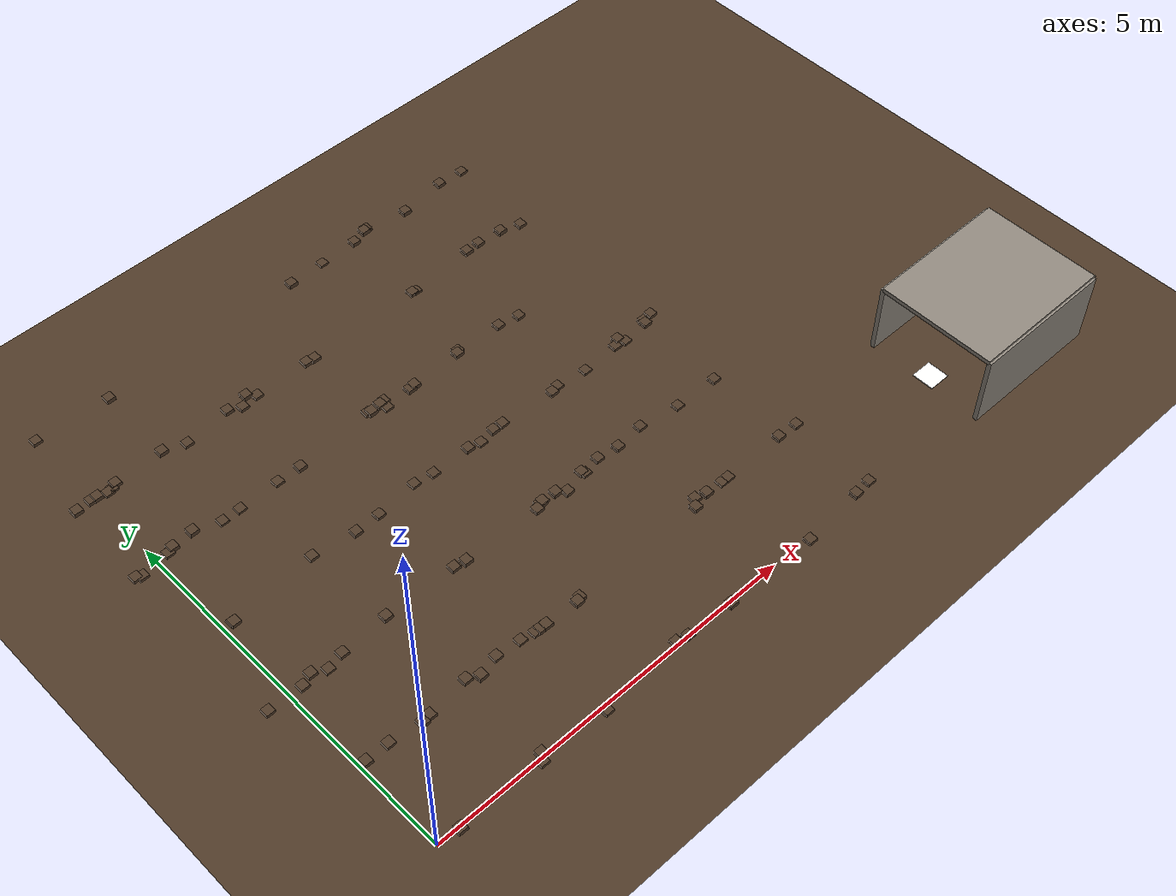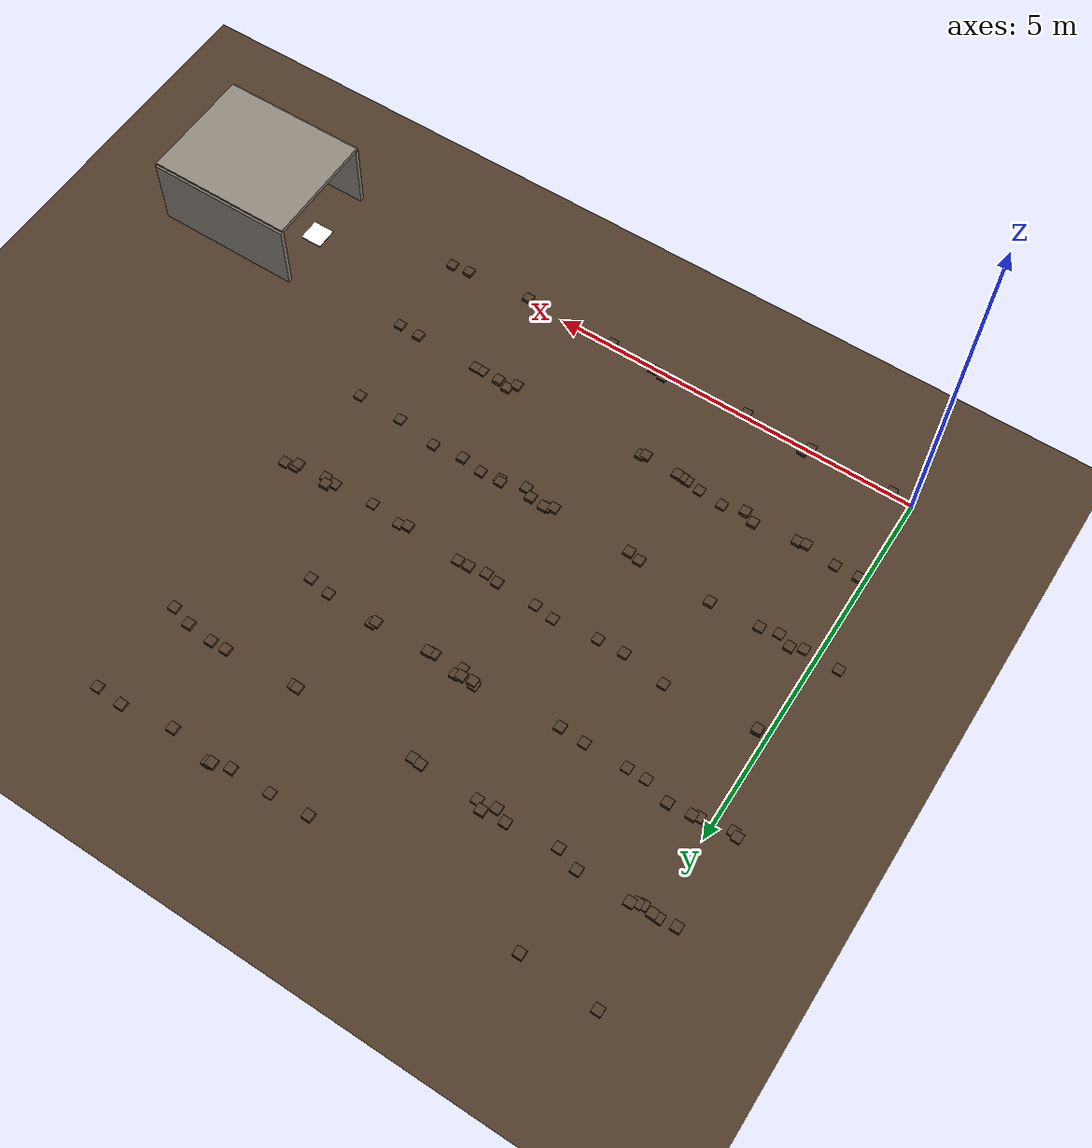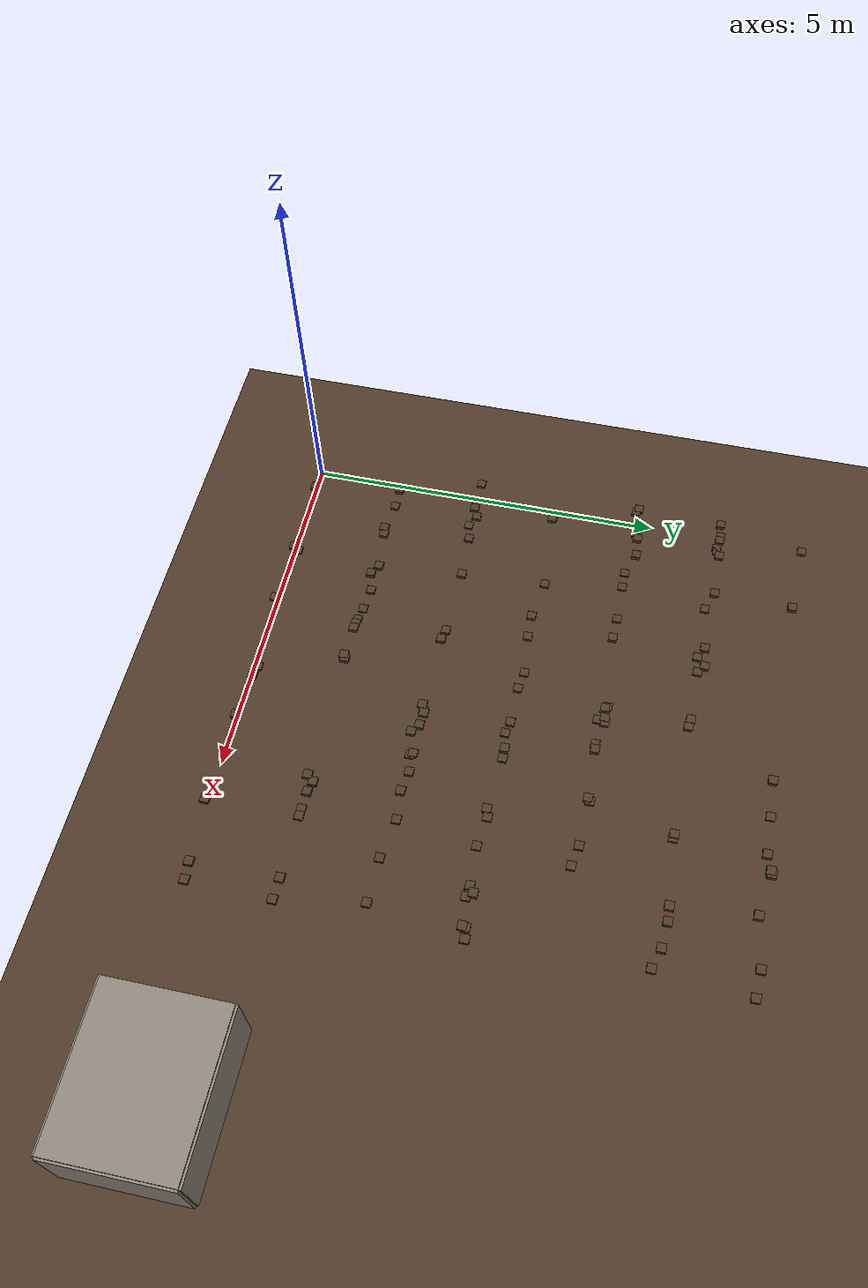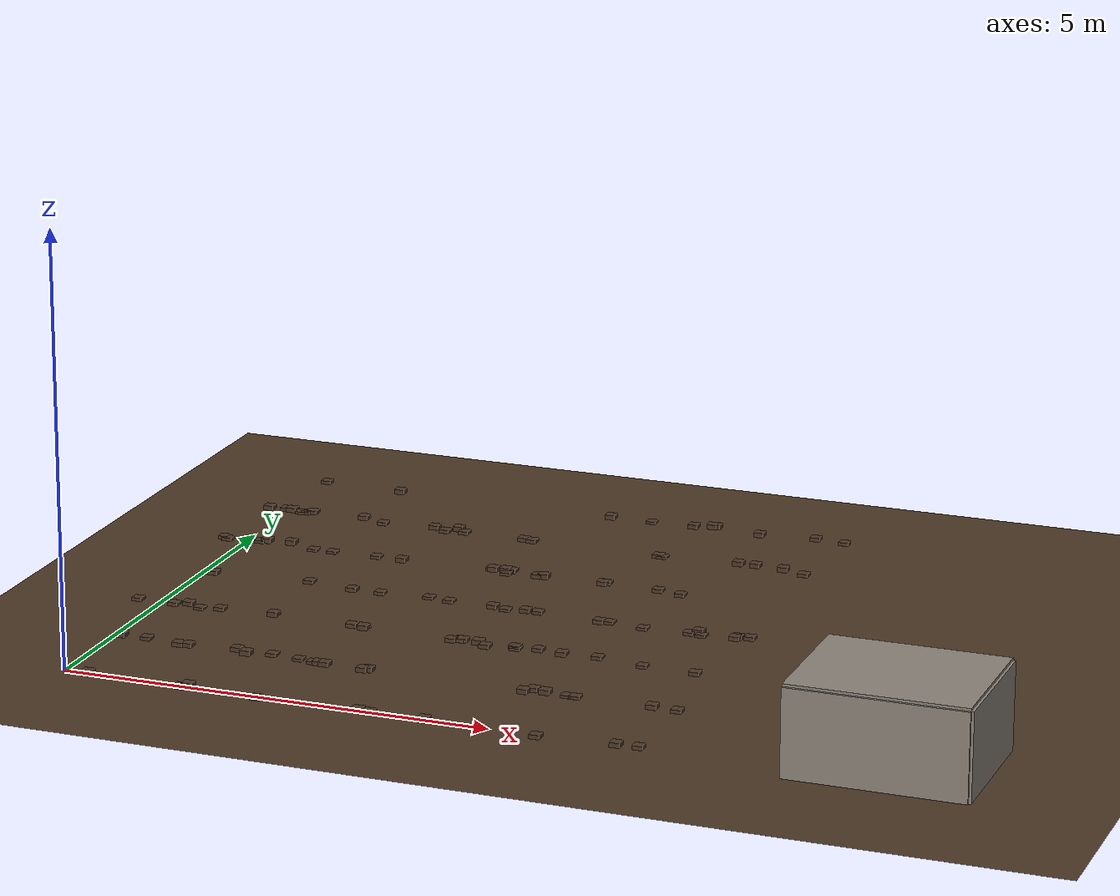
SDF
<sdf version="1.9">
 <world name="field_main">
  <physics name="1ms" type="ignored">
   <max_step_size>0.001</max_step_size>
   <real_time_factor>1.0</real_time_factor>
  </physics>
  <plugin filename="ignition-gazebo-physics-system" name="ignition::gazebo::systems::Physics"/>
  <plugin filename="ignition-gazebo-sensors-system" name="ignition::gazebo::systems::Sensors">
   <render_engine>ogre2</render_engine>
  </plugin>
  <plugin filename="ignition-gazebo-scene-broadcaster-system" name="ignition::gazebo::systems::SceneBroadcaster"/>
  <plugin filename="ignition-gazebo-user-commands-system" name="ignition::gazebo::systems::UserCommands"/>
  <plugin filename="ignition-gazebo-imu-system" name="ignition::gazebo::systems::Imu"/>
  <scene><ambient>0.5 0.5 0.5 1</ambient><background>0.7 0.8 0.9 1</background></scene>
  <light type="directional" name="sun">
   <pose>0 0 10 0 0 0</pose>
   <diffuse>1 1 1 1</diffuse>
   <specular>0.3 0.3 0.3 1</specular>
   <direction>-0.4 0.4 -0.85</direction>
  </light>
  <model name="furrow_floor">
   <static>true</static>
   <link name="link">
    <pose>0 0 0 0.05236 0 0</pose>
    <collision name="c">
     <geometry><plane><normal>0 0 1</normal><size>200 200</size></plane></geometry>
     <surface><friction><ode><mu>0.4</mu><mu2>0.4</mu2></ode></friction></surface>
    </collision>
    <visual name="v">
     <geometry><plane><normal>0 0 1</normal><size>200 200</size></plane></geometry>
     <material><ambient>0.20 0.15 0.10 1</ambient><diffuse>0.30 0.22 0.15 1</diffuse></material>
    </visual>
   </link>
  </model>
  <model name="clod_0_0">
   <static>true</static>
   <link name="l">
    <collision name="c">
     <geometry><box><size>0.12 0.12 0.059</size></box></geometry>
     <surface><friction><ode><mu>0.4</mu><mu2>0.4</mu2></ode></friction></surface>
    </collision>
    <visual name="v">
     <geometry><box><size>0.12 0.12 0.059</size></box></geometry>
     <material><ambient>0.22 0.16 0.11 1</ambient><diffuse>0.30 0.22 0.15 1</diffuse></material>
    </visual>
    <pose>0.290 -0.027 0.029 0 0 0</pose>
   </link>
  </model>
  <model name="clod_0_1">
   <static>true</static>
   <link name="l">
    <collision name="c">
     <geometry><box><size>0.12 0.12 0.045</size></box></geometry>
     <surface><friction><ode><mu>0.4</mu><mu2>0.4</mu2></ode></friction></surface>
    </collision>
    <visual name="v">
     <geometry><box><size>0.12 0.12 0.045</size></box></geometry>
     <material><ambient>0.22 0.16 0.11 1</ambient><diffuse>0.30 0.22 0.15 1</diffuse></material>
    </visual>
    <pose>6.665 0.052 0.022 0 0 0</pose>
   </link>
  </model>
  <model name="clod_0_2">
   <static>true</static>
   <link name="l">
    <collision name="c">
     <geometry><box><size>0.12 0.12 0.047</size></box></geometry>
     <surface><friction><ode><mu>0.4</mu><mu2>0.4</mu2></ode></friction></surface>
    </collision>
    <visual name="v">
     <geometry><box><size>0.12 0.12 0.047</size></box></geometry>
     <material><ambient>0.22 0.16 0.11 1</ambient><diffuse>0.30 0.22 0.15 1</diffuse></material>
    </visual>
    <pose>1.472 0.044 0.024 0 0 0</pose>
   </link>
  </model>
  <model name="clod_0_3">
   <static>true</static>
   <link name="l">
    <collision name="c">
     <geometry><box><size>0.12 0.12 0.034</size></box></geometry>
     <surface><friction><ode><mu>0.4</mu><mu2>0.4</mu2></ode></friction></surface>
    </collision>
    <visual name="v">
     <geometry><box><size>0.12 0.12 0.034</size></box></geometry>
     <material><ambient>0.22 0.16 0.11 1</ambient><diffuse>0.30 0.22 0.15 1</diffuse></material>
    </visual>
    <pose>3.624 0.011 0.017 0 0 0</pose>
   </link>
  </model>
  <model name="clod_0_4">
   <static>true</static>
   <link name="l">
    <collision name="c">
     <geometry><box><size>0.12 0.12 0.048</size></box></geometry>
     <surface><friction><ode><mu>0.4</mu><mu2>0.4</mu2></ode></friction></surface>
    </collision>
    <visual name="v">
     <geometry><box><size>0.12 0.12 0.048</size></box></geometry>
     <material><ambient>0.22 0.16 0.11 1</ambient><diffuse>0.30 0.22 0.15 1</diffuse></material>
    </visual>
    <pose>5.547 -0.045 0.024 0 0 0</pose>
   </link>
  </model>
  <model name="clod_0_5">
   <static>true</static>
   <link name="l">
    <collision name="c">
     <geometry><box><size>0.12 0.12 0.054</size></box></geometry>
     <surface><friction><ode><mu>0.4</mu><mu2>0.4</mu2></ode></friction></surface>
    </collision>
    <visual name="v">
     <geometry><box><size>0.12 0.12 0.054</size></box></geometry>
     <material><ambient>0.22 0.16 0.11 1</ambient><diffuse>0.30 0.22 0.15 1</diffuse></material>
    </visual>
    <pose>6.421 0.030 0.027 0 0 0</pose>
   </link>
  </model>
  <model name="clod_0_6">
   <static>true</static>
   <link name="l">
    <collision name="c">
     <geometry><box><size>0.12 0.12 0.060</size></box></geometry>
     <surface><friction><ode><mu>0.4</mu><mu2>0.4</mu2></ode></friction></surface>
    </collision>
    <visual name="v">
     <geometry><box><size>0.12 0.12 0.060</size></box></geometry>
     <material><ambient>0.22 0.16 0.11 1</ambient><diffuse>0.30 0.22 0.15 1</diffuse></material>
    </visual>
    <pose>4.269 -0.026 0.030 0 0 0</pose>
   </link>
  </model>
  <model name="clod_0_7">
   <static>true</static>
   <link name="l">
    <collision name="c">
     <geometry><box><size>0.12 0.12 0.045</size></box></geometry>
     <surface><friction><ode><mu>0.4</mu><mu2>0.4</mu2></ode></friction></surface>
    </collision>
    <visual name="v">
     <geometry><box><size>0.12 0.12 0.045</size></box></geometry>
     <material><ambient>0.22 0.16 0.11 1</ambient><diffuse>0.30 0.22 0.15 1</diffuse></material>
    </visual>
    <pose>1.412 -0.037 0.022 0 0 0</pose>
   </link>
  </model>
  <model name="clod_0_8">
   <static>true</static>
   <link name="l">
    <collision name="c">
     <geometry><box><size>0.12 0.12 0.041</size></box></geometry>
     <surface><friction><ode><mu>0.4</mu><mu2>0.4</mu2></ode></friction></surface>
    </collision>
    <visual name="v">
     <geometry><box><size>0.12 0.12 0.041</size></box></geometry>
     <material><ambient>0.22 0.16 0.11 1</ambient><diffuse>0.30 0.22 0.15 1</diffuse></material>
    </visual>
    <pose>2.326 -0.057 0.020 0 0 0</pose>
   </link>
  </model>
  <model name="clod_0_9">
   <static>true</static>
   <link name="l">
    <collision name="c">
     <geometry><box><size>0.12 0.12 0.032</size></box></geometry>
     <surface><friction><ode><mu>0.4</mu><mu2>0.4</mu2></ode></friction></surface>
    </collision>
    <visual name="v">
     <geometry><box><size>0.12 0.12 0.032</size></box></geometry>
     <material><ambient>0.22 0.16 0.11 1</ambient><diffuse>0.30 0.22 0.15 1</diffuse></material>
    </visual>
    <pose>3.473 0.043 0.016 0 0 0</pose>
   </link>
  </model>
  <model name="clod_0_10">
   <static>true</static>
   <link name="l">
    <collision name="c">
     <geometry><box><size>0.12 0.12 0.051</size></box></geometry>
     <surface><friction><ode><mu>0.4</mu><mu2>0.4</mu2></ode></friction></surface>
    </collision>
    <visual name="v">
     <geometry><box><size>0.12 0.12 0.051</size></box></geometry>
     <material><ambient>0.22 0.16 0.11 1</ambient><diffuse>0.30 0.22 0.15 1</diffuse></material>
    </visual>
    <pose>2.595 1.173 0.026 0 0 0</pose>
   </link>
  </model>
  <model name="clod_0_11">
   <static>true</static>
   <link name="l">
    <collision name="c">
     <geometry><box><size>0.12 0.12 0.052</size></box></geometry>
     <surface><friction><ode><mu>0.4</mu><mu2>0.4</mu2></ode></friction></surface>
    </collision>
    <visual name="v">
     <geometry><box><size>0.12 0.12 0.052</size></box></geometry>
     <material><ambient>0.22 0.16 0.11 1</ambient><diffuse>0.30 0.22 0.15 1</diffuse></material>
    </visual>
    <pose>0.817 1.170 0.026 0 0 0</pose>
   </link>
  </model>
  <model name="clod_0_12">
   <static>true</static>
   <link name="l">
    <collision name="c">
     <geometry><box><size>0.12 0.12 0.040</size></box></geometry>
     <surface><friction><ode><mu>0.4</mu><mu2>0.4</mu2></ode></friction></surface>
    </collision>
    <visual name="v">
     <geometry><box><size>0.12 0.12 0.040</size></box></geometry>
     <material><ambient>0.22 0.16 0.11 1</ambient><diffuse>0.30 0.22 0.15 1</diffuse></material>
    </visual>
    <pose>1.927 1.249 0.020 0 0 0</pose>
   </link>
  </model>
  <model name="clod_0_13">
   <static>true</static>
   <link name="l">
    <collision name="c">
     <geometry><box><size>0.12 0.12 0.059</size></box></geometry>
     <surface><friction><ode><mu>0.4</mu><mu2>0.4</mu2></ode></friction></surface>
    </collision>
    <visual name="v">
     <geometry><box><size>0.12 0.12 0.059</size></box></geometry>
     <material><ambient>0.22 0.16 0.11 1</ambient><diffuse>0.30 0.22 0.15 1</diffuse></material>
    </visual>
    <pose>1.643 1.177 0.030 0 0 0</pose>
   </link>
  </model>
  <model name="clod_0_14">
   <static>true</static>
   <link name="l">
    <collision name="c">
     <geometry><box><size>0.12 0.12 0.054</size></box></geometry>
     <surface><friction><ode><mu>0.4</mu><mu2>0.4</mu2></ode></friction></surface>
    </collision>
    <visual name="v">
     <geometry><box><size>0.12 0.12 0.054</size></box></geometry>
     <material><ambient>0.22 0.16 0.11 1</ambient><diffuse>0.30 0.22 0.15 1</diffuse></material>
    </visual>
    <pose>4.937 1.166 0.027 0 0 0</pose>
   </link>
  </model>
  <model name="clod_0_15">
   <static>true</static>
   <link name="l">
    <collision name="c">
     <geometry><box><size>0.12 0.12 0.053</size></box></geometry>
     <surface><friction><ode><mu>0.4</mu><mu2>0.4</mu2></ode></friction></surface>
    </collision>
    <visual name="v">
     <geometry><box><size>0.12 0.12 0.053</size></box></geometry>
     <material><ambient>0.22 0.16 0.11 1</ambient><diffuse>0.30 0.22 0.15 1</diffuse></material>
    </visual>
    <pose>3.054 1.155 0.027 0 0 0</pose>
   </link>
  </model>
  <model name="clod_0_16">
   <static>true</static>
   <link name="l">
    <collision name="c">
     <geometry><box><size>0.12 0.12 0.035</size></box></geometry>
     <surface><friction><ode><mu>0.4</mu><mu2>0.4</mu2></ode></friction></surface>
    </collision>
    <visual name="v">
     <geometry><box><size>0.12 0.12 0.035</size></box></geometry>
     <material><ambient>0.22 0.16 0.11 1</ambient><diffuse>0.30 0.22 0.15 1</diffuse></material>
    </visual>
    <pose>2.445 1.186 0.018 0 0 0</pose>
   </link>
  </model>
  <model name="clod_0_17">
   <static>true</static>
   <link name="l">
    <collision name="c">
     <geometry><box><size>0.12 0.12 0.042</size></box></geometry>
     <surface><friction><ode><mu>0.4</mu><mu2>0.4</mu2></ode></friction></surface>
    </collision>
    <visual name="v">
     <geometry><box><size>0.12 0.12 0.042</size></box></geometry>
     <material><ambient>0.22 0.16 0.11 1</ambient><diffuse>0.30 0.22 0.15 1</diffuse></material>
    </visual>
    <pose>6.690 1.206 0.021 0 0 0</pose>
   </link>
  </model>
  <model name="clod_0_18">
   <static>true</static>
   <link name="l">
    <collision name="c">
     <geometry><box><size>0.12 0.12 0.048</size></box></geometry>
     <surface><friction><ode><mu>0.4</mu><mu2>0.4</mu2></ode></friction></surface>
    </collision>
    <visual name="v">
     <geometry><box><size>0.12 0.12 0.048</size></box></geometry>
     <material><ambient>0.22 0.16 0.11 1</ambient><diffuse>0.30 0.22 0.15 1</diffuse></material>
    </visual>
    <pose>5.020 1.260 0.024 0 0 0</pose>
   </link>
  </model>
  <model name="clod_0_19">
   <static>true</static>
   <link name="l">
    <collision name="c">
     <geometry><box><size>0.12 0.12 0.054</size></box></geometry>
     <surface><friction><ode><mu>0.4</mu><mu2>0.4</mu2></ode></friction></surface>
    </collision>
    <visual name="v">
     <geometry><box><size>0.12 0.12 0.054</size></box></geometry>
     <material><ambient>0.22 0.16 0.11 1</ambient><diffuse>0.30 0.22 0.15 1</diffuse></material>
    </visual>
    <pose>6.399 1.217 0.027 0 0 0</pose>
   </link>
  </model>
  <model name="clod_1_0">
   <static>true</static>
   <link name="l">
    <collision name="c">
     <geometry><box><size>0.12 0.12 0.041</size></box></geometry>
     <surface><friction><ode><mu>0.4</mu><mu2>0.4</mu2></ode></friction></surface>
    </collision>
    <visual name="v">
     <geometry><box><size>0.12 0.12 0.041</size></box></geometry>
     <material><ambient>0.22 0.16 0.11 1</ambient><diffuse>0.30 0.22 0.15 1</diffuse></material>
    </visual>
    <pose>0.395 1.228 0.021 0 0 0</pose>
   </link>
  </model>
  <model name="clod_1_1">
   <static>true</static>
   <link name="l">
    <collision name="c">
     <geometry><box><size>0.12 0.12 0.031</size></box></geometry>
     <surface><friction><ode><mu>0.4</mu><mu2>0.4</mu2></ode></friction></surface>
    </collision>
    <visual name="v">
     <geometry><box><size>0.12 0.12 0.031</size></box></geometry>
     <material><ambient>0.22 0.16 0.11 1</ambient><diffuse>0.30 0.22 0.15 1</diffuse></material>
    </visual>
    <pose>5.423 1.215 0.016 0 0 0</pose>
   </link>
  </model>
  <model name="clod_1_2">
   <static>true</static>
   <link name="l">
    <collision name="c">
     <geometry><box><size>0.12 0.12 0.050</size></box></geometry>
     <surface><friction><ode><mu>0.4</mu><mu2>0.4</mu2></ode></friction></surface>
    </collision>
    <visual name="v">
     <geometry><box><size>0.12 0.12 0.050</size></box></geometry>
     <material><ambient>0.22 0.16 0.11 1</ambient><diffuse>0.30 0.22 0.15 1</diffuse></material>
    </visual>
    <pose>1.495 1.257 0.025 0 0 0</pose>
   </link>
  </model>
  <model name="clod_1_3">
   <static>true</static>
   <link name="l">
    <collision name="c">
     <geometry><box><size>0.12 0.12 0.034</size></box></geometry>
     <surface><friction><ode><mu>0.4</mu><mu2>0.4</mu2></ode></friction></surface>
    </collision>
    <visual name="v">
     <geometry><box><size>0.12 0.12 0.034</size></box></geometry>
     <material><ambient>0.22 0.16 0.11 1</ambient><diffuse>0.30 0.22 0.15 1</diffuse></material>
    </visual>
    <pose>5.524 1.215 0.017 0 0 0</pose>
   </link>
  </model>
  <model name="clod_1_4">
   <static>true</static>
   <link name="l">
    <collision name="c">
     <geometry><box><size>0.12 0.12 0.056</size></box></geometry>
     <surface><friction><ode><mu>0.4</mu><mu2>0.4</mu2></ode></friction></surface>
    </collision>
    <visual name="v">
     <geometry><box><size>0.12 0.12 0.056</size></box></geometry>
     <material><ambient>0.22 0.16 0.11 1</ambient><diffuse>0.30 0.22 0.15 1</diffuse></material>
    </visual>
    <pose>5.173 1.223 0.028 0 0 0</pose>
   </link>
  </model>
  <model name="clod_1_5">
   <static>true</static>
   <link name="l">
    <collision name="c">
     <geometry><box><size>0.12 0.12 0.049</size></box></geometry>
     <surface><friction><ode><mu>0.4</mu><mu2>0.4</mu2></ode></friction></surface>
    </collision>
    <visual name="v">
     <geometry><box><size>0.12 0.12 0.049</size></box></geometry>
     <material><ambient>0.22 0.16 0.11 1</ambient><diffuse>0.30 0.22 0.15 1</diffuse></material>
    </visual>
    <pose>2.518 1.177 0.025 0 0 0</pose>
   </link>
  </model>
  <model name="clod_1_6">
   <static>true</static>
   <link name="l">
    <collision name="c">
     <geometry><box><size>0.12 0.12 0.049</size></box></geometry>
     <surface><friction><ode><mu>0.4</mu><mu2>0.4</mu2></ode></friction></surface>
    </collision>
    <visual name="v">
     <geometry><box><size>0.12 0.12 0.049</size></box></geometry>
     <material><ambient>0.22 0.16 0.11 1</ambient><diffuse>0.30 0.22 0.15 1</diffuse></material>
    </visual>
    <pose>0.924 1.188 0.025 0 0 0</pose>
   </link>
  </model>
  <model name="clod_1_7">
   <static>true</static>
   <link name="l">
    <collision name="c">
     <geometry><box><size>0.12 0.12 0.033</size></box></geometry>
     <surface><friction><ode><mu>0.4</mu><mu2>0.4</mu2></ode></friction></surface>
    </collision>
    <visual name="v">
     <geometry><box><size>0.12 0.12 0.033</size></box></geometry>
     <material><ambient>0.22 0.16 0.11 1</ambient><diffuse>0.30 0.22 0.15 1</diffuse></material>
    </visual>
    <pose>2.257 1.220 0.017 0 0 0</pose>
   </link>
  </model>
  <model name="clod_1_8">
   <static>true</static>
   <link name="l">
    <collision name="c">
     <geometry><box><size>0.12 0.12 0.055</size></box></geometry>
     <surface><friction><ode><mu>0.4</mu><mu2>0.4</mu2></ode></friction></surface>
    </collision>
    <visual name="v">
     <geometry><box><size>0.12 0.12 0.055</size></box></geometry>
     <material><ambient>0.22 0.16 0.11 1</ambient><diffuse>0.30 0.22 0.15 1</diffuse></material>
    </visual>
    <pose>0.084 1.222 0.027 0 0 0</pose>
   </link>
  </model>
  <model name="clod_1_9">
   <static>true</static>
   <link name="l">
    <collision name="c">
     <geometry><box><size>0.12 0.12 0.052</size></box></geometry>
     <surface><friction><ode><mu>0.4</mu><mu2>0.4</mu2></ode></friction></surface>
    </collision>
    <visual name="v">
     <geometry><box><size>0.12 0.12 0.052</size></box></geometry>
     <material><ambient>0.22 0.16 0.11 1</ambient><diffuse>0.30 0.22 0.15 1</diffuse></material>
    </visual>
    <pose>3.106 1.182 0.026 0 0 0</pose>
   </link>
  </model>
  <model name="clod_1_10">
   <static>true</static>
   <link name="l">
    <collision name="c">
     <geometry><box><size>0.12 0.12 0.057</size></box></geometry>
     <surface><friction><ode><mu>0.4</mu><mu2>0.4</mu2></ode></friction></surface>
    </collision>
    <visual name="v">
     <geometry><box><size>0.12 0.12 0.057</size></box></geometry>
     <material><ambient>0.22 0.16 0.11 1</ambient><diffuse>0.30 0.22 0.15 1</diffuse></material>
    </visual>
    <pose>3.913 2.427 0.028 0 0 0</pose>
   </link>
  </model>
  <model name="clod_1_11">
   <static>true</static>
   <link name="l">
    <collision name="c">
     <geometry><box><size>0.12 0.12 0.043</size></box></geometry>
     <surface><friction><ode><mu>0.4</mu><mu2>0.4</mu2></ode></friction></surface>
    </collision>
    <visual name="v">
     <geometry><box><size>0.12 0.12 0.043</size></box></geometry>
     <material><ambient>0.22 0.16 0.11 1</ambient><diffuse>0.30 0.22 0.15 1</diffuse></material>
    </visual>
    <pose>0.746 2.423 0.021 0 0 0</pose>
   </link>
  </model>
  <model name="clod_1_12">
   <static>true</static>
   <link name="l">
    <collision name="c">
     <geometry><box><size>0.12 0.12 0.049</size></box></geometry>
     <surface><friction><ode><mu>0.4</mu><mu2>0.4</mu2></ode></friction></surface>
    </collision>
    <visual name="v">
     <geometry><box><size>0.12 0.12 0.049</size></box></geometry>
     <material><ambient>0.22 0.16 0.11 1</ambient><diffuse>0.30 0.22 0.15 1</diffuse></material>
    </visual>
    <pose>4.029 2.343 0.024 0 0 0</pose>
   </link>
  </model>
  <model name="clod_1_13">
   <static>true</static>
   <link name="l">
    <collision name="c">
     <geometry><box><size>0.12 0.12 0.047</size></box></geometry>
     <surface><friction><ode><mu>0.4</mu><mu2>0.4</mu2></ode></friction></surface>
    </collision>
    <visual name="v">
     <geometry><box><size>0.12 0.12 0.047</size></box></geometry>
     <material><ambient>0.22 0.16 0.11 1</ambient><diffuse>0.30 0.22 0.15 1</diffuse></material>
    </visual>
    <pose>3.598 2.395 0.024 0 0 0</pose>
   </link>
  </model>
  <model name="clod_1_14">
   <static>true</static>
   <link name="l">
    <collision name="c">
     <geometry><box><size>0.12 0.12 0.048</size></box></geometry>
     <surface><friction><ode><mu>0.4</mu><mu2>0.4</mu2></ode></friction></surface>
    </collision>
    <visual name="v">
     <geometry><box><size>0.12 0.12 0.048</size></box></geometry>
     <material><ambient>0.22 0.16 0.11 1</ambient><diffuse>0.30 0.22 0.15 1</diffuse></material>
    </visual>
    <pose>0.334 2.454 0.024 0 0 0</pose>
   </link>
  </model>
  <model name="clod_1_15">
   <static>true</static>
   <link name="l">
    <collision name="c">
     <geometry><box><size>0.12 0.12 0.047</size></box></geometry>
     <surface><friction><ode><mu>0.4</mu><mu2>0.4</mu2></ode></friction></surface>
    </collision>
    <visual name="v">
     <geometry><box><size>0.12 0.12 0.047</size></box></geometry>
     <material><ambient>0.22 0.16 0.11 1</ambient><diffuse>0.30 0.22 0.15 1</diffuse></material>
    </visual>
    <pose>2.370 2.443 0.023 0 0 0</pose>
   </link>
  </model>
  <model name="clod_1_16">
   <static>true</static>
   <link name="l">
    <collision name="c">
     <geometry><box><size>0.12 0.12 0.031</size></box></geometry>
     <surface><friction><ode><mu>0.4</mu><mu2>0.4</mu2></ode></friction></surface>
    </collision>
    <visual name="v">
     <geometry><box><size>0.12 0.12 0.031</size></box></geometry>
     <material><ambient>0.22 0.16 0.11 1</ambient><diffuse>0.30 0.22 0.15 1</diffuse></material>
    </visual>
    <pose>0.512 2.370 0.016 0 0 0</pose>
   </link>
  </model>
  <model name="clod_1_17">
   <static>true</static>
   <link name="l">
    <collision name="c">
     <geometry><box><size>0.12 0.12 0.053</size></box></geometry>
     <surface><friction><ode><mu>0.4</mu><mu2>0.4</mu2></ode></friction></surface>
    </collision>
    <visual name="v">
     <geometry><box><size>0.12 0.12 0.053</size></box></geometry>
     <material><ambient>0.22 0.16 0.11 1</ambient><diffuse>0.30 0.22 0.15 1</diffuse></material>
    </visual>
    <pose>4.913 2.414 0.026 0 0 0</pose>
   </link>
  </model>
  <model name="clod_1_18">
   <static>true</static>
   <link name="l">
    <collision name="c">
     <geometry><box><size>0.12 0.12 0.042</size></box></geometry>
     <surface><friction><ode><mu>0.4</mu><mu2>0.4</mu2></ode></friction></surface>
    </collision>
    <visual name="v">
     <geometry><box><size>0.12 0.12 0.042</size></box></geometry>
     <material><ambient>0.22 0.16 0.11 1</ambient><diffuse>0.30 0.22 0.15 1</diffuse></material>
    </visual>
    <pose>5.319 2.455 0.021 0 0 0</pose>
   </link>
  </model>
  <model name="clod_1_19">
   <static>true</static>
   <link name="l">
    <collision name="c">
     <geometry><box><size>0.12 0.12 0.042</size></box></geometry>
     <surface><friction><ode><mu>0.4</mu><mu2>0.4</mu2></ode></friction></surface>
    </collision>
    <visual name="v">
     <geometry><box><size>0.12 0.12 0.042</size></box></geometry>
     <material><ambient>0.22 0.16 0.11 1</ambient><diffuse>0.30 0.22 0.15 1</diffuse></material>
    </visual>
    <pose>0.179 2.390 0.021 0 0 0</pose>
   </link>
  </model>
  <model name="clod_2_0">
   <static>true</static>
   <link name="l">
    <collision name="c">
     <geometry><box><size>0.12 0.12 0.030</size></box></geometry>
     <surface><friction><ode><mu>0.4</mu><mu2>0.4</mu2></ode></friction></surface>
    </collision>
    <visual name="v">
     <geometry><box><size>0.12 0.12 0.030</size></box></geometry>
     <material><ambient>0.22 0.16 0.11 1</ambient><diffuse>0.30 0.22 0.15 1</diffuse></material>
    </visual>
    <pose>4.367 2.405 0.015 0 0 0</pose>
   </link>
  </model>
  <model name="clod_2_1">
   <static>true</static>
   <link name="l">
    <collision name="c">
     <geometry><box><size>0.12 0.12 0.045</size></box></geometry>
     <surface><friction><ode><mu>0.4</mu><mu2>0.4</mu2></ode></friction></surface>
    </collision>
    <visual name="v">
     <geometry><box><size>0.12 0.12 0.045</size></box></geometry>
     <material><ambient>0.22 0.16 0.11 1</ambient><diffuse>0.30 0.22 0.15 1</diffuse></material>
    </visual>
    <pose>6.491 2.364 0.022 0 0 0</pose>
   </link>
  </model>
  <model name="clod_2_2">
   <static>true</static>
   <link name="l">
    <collision name="c">
     <geometry><box><size>0.12 0.12 0.040</size></box></geometry>
     <surface><friction><ode><mu>0.4</mu><mu2>0.4</mu2></ode></friction></surface>
    </collision>
    <visual name="v">
     <geometry><box><size>0.12 0.12 0.040</size></box></geometry>
     <material><ambient>0.22 0.16 0.11 1</ambient><diffuse>0.30 0.22 0.15 1</diffuse></material>
    </visual>
    <pose>4.343 2.443 0.020 0 0 0</pose>
   </link>
  </model>
  <model name="clod_2_3">
   <static>true</static>
   <link name="l">
    <collision name="c">
     <geometry><box><size>0.12 0.12 0.036</size></box></geometry>
     <surface><friction><ode><mu>0.4</mu><mu2>0.4</mu2></ode></friction></surface>
    </collision>
    <visual name="v">
     <geometry><box><size>0.12 0.12 0.036</size></box></geometry>
     <material><ambient>0.22 0.16 0.11 1</ambient><diffuse>0.30 0.22 0.15 1</diffuse></material>
    </visual>
    <pose>5.875 2.375 0.018 0 0 0</pose>
   </link>
  </model>
  <model name="clod_2_4">
   <static>true</static>
   <link name="l">
    <collision name="c">
     <geometry><box><size>0.12 0.12 0.044</size></box></geometry>
     <surface><friction><ode><mu>0.4</mu><mu2>0.4</mu2></ode></friction></surface>
    </collision>
    <visual name="v">
     <geometry><box><size>0.12 0.12 0.044</size></box></geometry>
     <material><ambient>0.22 0.16 0.11 1</ambient><diffuse>0.30 0.22 0.15 1</diffuse></material>
    </visual>
    <pose>3.682 2.431 0.022 0 0 0</pose>
   </link>
  </model>
  <model name="clod_2_5">
   <static>true</static>
   <link name="l">
    <collision name="c">
     <geometry><box><size>0.12 0.12 0.056</size></box></geometry>
     <surface><friction><ode><mu>0.4</mu><mu2>0.4</mu2></ode></friction></surface>
    </collision>
    <visual name="v">
     <geometry><box><size>0.12 0.12 0.056</size></box></geometry>
     <material><ambient>0.22 0.16 0.11 1</ambient><diffuse>0.30 0.22 0.15 1</diffuse></material>
    </visual>
    <pose>1.392 2.458 0.028 0 0 0</pose>
   </link>
  </model>
  <model name="clod_2_6">
   <static>true</static>
   <link name="l">
    <collision name="c">
     <geometry><box><size>0.12 0.12 0.045</size></box></geometry>
     <surface><friction><ode><mu>0.4</mu><mu2>0.4</mu2></ode></friction></surface>
    </collision>
    <visual name="v">
     <geometry><box><size>0.12 0.12 0.045</size></box></geometry>
     <material><ambient>0.22 0.16 0.11 1</ambient><diffuse>0.30 0.22 0.15 1</diffuse></material>
    </visual>
    <pose>3.719 2.443 0.022 0 0 0</pose>
   </link>
  </model>
  <model name="clod_2_7">
   <static>true</static>
   <link name="l">
    <collision name="c">
     <geometry><box><size>0.12 0.12 0.057</size></box></geometry>
     <surface><friction><ode><mu>0.4</mu><mu2>0.4</mu2></ode></friction></surface>
    </collision>
    <visual name="v">
     <geometry><box><size>0.12 0.12 0.057</size></box></geometry>
     <material><ambient>0.22 0.16 0.11 1</ambient><diffuse>0.30 0.22 0.15 1</diffuse></material>
    </visual>
    <pose>2.526 2.412 0.029 0 0 0</pose>
   </link>
  </model>
  <model name="clod_2_8">
   <static>true</static>
   <link name="l">
    <collision name="c">
     <geometry><box><size>0.12 0.12 0.039</size></box></geometry>
     <surface><friction><ode><mu>0.4</mu><mu2>0.4</mu2></ode></friction></surface>
    </collision>
    <visual name="v">
     <geometry><box><size>0.12 0.12 0.039</size></box></geometry>
     <material><ambient>0.22 0.16 0.11 1</ambient><diffuse>0.30 0.22 0.15 1</diffuse></material>
    </visual>
    <pose>-0.281 2.398 0.019 0 0 0</pose>
   </link>
  </model>
  <model name="clod_2_9">
   <static>true</static>
   <link name="l">
    <collision name="c">
     <geometry><box><size>0.12 0.12 0.044</size></box></geometry>
     <surface><friction><ode><mu>0.4</mu><mu2>0.4</mu2></ode></friction></surface>
    </collision>
    <visual name="v">
     <geometry><box><size>0.12 0.12 0.044</size></box></geometry>
     <material><ambient>0.22 0.16 0.11 1</ambient><diffuse>0.30 0.22 0.15 1</diffuse></material>
    </visual>
    <pose>4.619 2.456 0.022 0 0 0</pose>
   </link>
  </model>
  <model name="clod_2_10">
   <static>true</static>
   <link name="l">
    <collision name="c">
     <geometry><box><size>0.12 0.12 0.033</size></box></geometry>
     <surface><friction><ode><mu>0.4</mu><mu2>0.4</mu2></ode></friction></surface>
    </collision>
    <visual name="v">
     <geometry><box><size>0.12 0.12 0.033</size></box></geometry>
     <material><ambient>0.22 0.16 0.11 1</ambient><diffuse>0.30 0.22 0.15 1</diffuse></material>
    </visual>
    <pose>2.815 3.648 0.016 0 0 0</pose>
   </link>
  </model>
  <model name="clod_2_11">
   <static>true</static>
   <link name="l">
    <collision name="c">
     <geometry><box><size>0.12 0.12 0.033</size></box></geometry>
     <surface><friction><ode><mu>0.4</mu><mu2>0.4</mu2></ode></friction></surface>
    </collision>
    <visual name="v">
     <geometry><box><size>0.12 0.12 0.033</size></box></geometry>
     <material><ambient>0.22 0.16 0.11 1</ambient><diffuse>0.30 0.22 0.15 1</diffuse></material>
    </visual>
    <pose>6.154 3.551 0.017 0 0 0</pose>
   </link>
  </model>
  <model name="clod_2_12">
   <static>true</static>
   <link name="l">
    <collision name="c">
     <geometry><box><size>0.12 0.12 0.038</size></box></geometry>
     <surface><friction><ode><mu>0.4</mu><mu2>0.4</mu2></ode></friction></surface>
    </collision>
    <visual name="v">
     <geometry><box><size>0.12 0.12 0.038</size></box></geometry>
     <material><ambient>0.22 0.16 0.11 1</ambient><diffuse>0.30 0.22 0.15 1</diffuse></material>
    </visual>
    <pose>4.168 3.617 0.019 0 0 0</pose>
   </link>
  </model>
  <model name="clod_2_13">
   <static>true</static>
   <link name="l">
    <collision name="c">
     <geometry><box><size>0.12 0.12 0.048</size></box></geometry>
     <surface><friction><ode><mu>0.4</mu><mu2>0.4</mu2></ode></friction></surface>
    </collision>
    <visual name="v">
     <geometry><box><size>0.12 0.12 0.048</size></box></geometry>
     <material><ambient>0.22 0.16 0.11 1</ambient><diffuse>0.30 0.22 0.15 1</diffuse></material>
    </visual>
    <pose>4.019 3.614 0.024 0 0 0</pose>
   </link>
  </model>
  <model name="clod_2_14">
   <static>true</static>
   <link name="l">
    <collision name="c">
     <geometry><box><size>0.12 0.12 0.049</size></box></geometry>
     <surface><friction><ode><mu>0.4</mu><mu2>0.4</mu2></ode></friction></surface>
    </collision>
    <visual name="v">
     <geometry><box><size>0.12 0.12 0.049</size></box></geometry>
     <material><ambient>0.22 0.16 0.11 1</ambient><diffuse>0.30 0.22 0.15 1</diffuse></material>
    </visual>
    <pose>0.141 3.546 0.024 0 0 0</pose>
   </link>
  </model>
  <model name="clod_2_15">
   <static>true</static>
   <link name="l">
    <collision name="c">
     <geometry><box><size>0.12 0.12 0.033</size></box></geometry>
     <surface><friction><ode><mu>0.4</mu><mu2>0.4</mu2></ode></friction></surface>
    </collision>
    <visual name="v">
     <geometry><box><size>0.12 0.12 0.033</size></box></geometry>
     <material><ambient>0.22 0.16 0.11 1</ambient><diffuse>0.30 0.22 0.15 1</diffuse></material>
    </visual>
    <pose>3.789 3.576 0.016 0 0 0</pose>
   </link>
  </model>
  <model name="clod_2_16">
   <static>true</static>
   <link name="l">
    <collision name="c">
     <geometry><box><size>0.12 0.12 0.042</size></box></geometry>
     <surface><friction><ode><mu>0.4</mu><mu2>0.4</mu2></ode></friction></surface>
    </collision>
    <visual name="v">
     <geometry><box><size>0.12 0.12 0.042</size></box></geometry>
     <material><ambient>0.22 0.16 0.11 1</ambient><diffuse>0.30 0.22 0.15 1</diffuse></material>
    </visual>
    <pose>1.311 3.653 0.021 0 0 0</pose>
   </link>
  </model>
  <model name="clod_2_17">
   <static>true</static>
   <link name="l">
    <collision name="c">
     <geometry><box><size>0.12 0.12 0.048</size></box></geometry>
     <surface><friction><ode><mu>0.4</mu><mu2>0.4</mu2></ode></friction></surface>
    </collision>
    <visual name="v">
     <geometry><box><size>0.12 0.12 0.048</size></box></geometry>
     <material><ambient>0.22 0.16 0.11 1</ambient><diffuse>0.30 0.22 0.15 1</diffuse></material>
    </visual>
    <pose>4.929 3.563 0.024 0 0 0</pose>
   </link>
  </model>
  <model name="clod_2_18">
   <static>true</static>
   <link name="l">
    <collision name="c">
     <geometry><box><size>0.12 0.12 0.041</size></box></geometry>
     <surface><friction><ode><mu>0.4</mu><mu2>0.4</mu2></ode></friction></surface>
    </collision>
    <visual name="v">
     <geometry><box><size>0.12 0.12 0.041</size></box></geometry>
     <material><ambient>0.22 0.16 0.11 1</ambient><diffuse>0.30 0.22 0.15 1</diffuse></material>
    </visual>
    <pose>2.234 3.584 0.020 0 0 0</pose>
   </link>
  </model>
  <model name="clod_2_19">
   <static>true</static>
   <link name="l">
    <collision name="c">
     <geometry><box><size>0.12 0.12 0.057</size></box></geometry>
     <surface><friction><ode><mu>0.4</mu><mu2>0.4</mu2></ode></friction></surface>
    </collision>
    <visual name="v">
     <geometry><box><size>0.12 0.12 0.057</size></box></geometry>
     <material><ambient>0.22 0.16 0.11 1</ambient><diffuse>0.30 0.22 0.15 1</diffuse></material>
    </visual>
    <pose>6.096 3.634 0.028 0 0 0</pose>
   </link>
  </model>
  <model name="clod_3_0">
   <static>true</static>
   <link name="l">
    <collision name="c">
     <geometry><box><size>0.12 0.12 0.030</size></box></geometry>
     <surface><friction><ode><mu>0.4</mu><mu2>0.4</mu2></ode></friction></surface>
    </collision>
    <visual name="v">
     <geometry><box><size>0.12 0.12 0.030</size></box></geometry>
     <material><ambient>0.22 0.16 0.11 1</ambient><diffuse>0.30 0.22 0.15 1</diffuse></material>
    </visual>
    <pose>0.132 3.561 0.015 0 0 0</pose>
   </link>
  </model>
  <model name="clod_3_1">
   <static>true</static>
   <link name="l">
    <collision name="c">
     <geometry><box><size>0.12 0.12 0.048</size></box></geometry>
     <surface><friction><ode><mu>0.4</mu><mu2>0.4</mu2></ode></friction></surface>
    </collision>
    <visual name="v">
     <geometry><box><size>0.12 0.12 0.048</size></box></geometry>
     <material><ambient>0.22 0.16 0.11 1</ambient><diffuse>0.30 0.22 0.15 1</diffuse></material>
    </visual>
    <pose>3.617 3.611 0.024 0 0 0</pose>
   </link>
  </model>
  <model name="clod_3_2">
   <static>true</static>
   <link name="l">
    <collision name="c">
     <geometry><box><size>0.12 0.12 0.047</size></box></geometry>
     <surface><friction><ode><mu>0.4</mu><mu2>0.4</mu2></ode></friction></surface>
    </collision>
    <visual name="v">
     <geometry><box><size>0.12 0.12 0.047</size></box></geometry>
     <material><ambient>0.22 0.16 0.11 1</ambient><diffuse>0.30 0.22 0.15 1</diffuse></material>
    </visual>
    <pose>6.555 3.635 0.023 0 0 0</pose>
   </link>
  </model>
  <model name="clod_3_3">
   <static>true</static>
   <link name="l">
    <collision name="c">
     <geometry><box><size>0.12 0.12 0.037</size></box></geometry>
     <surface><friction><ode><mu>0.4</mu><mu2>0.4</mu2></ode></friction></surface>
    </collision>
    <visual name="v">
     <geometry><box><size>0.12 0.12 0.037</size></box></geometry>
     <material><ambient>0.22 0.16 0.11 1</ambient><diffuse>0.30 0.22 0.15 1</diffuse></material>
    </visual>
    <pose>6.002 3.572 0.018 0 0 0</pose>
   </link>
  </model>
  <model name="clod_3_4">
   <static>true</static>
   <link name="l">
    <collision name="c">
     <geometry><box><size>0.12 0.12 0.048</size></box></geometry>
     <surface><friction><ode><mu>0.4</mu><mu2>0.4</mu2></ode></friction></surface>
    </collision>
    <visual name="v">
     <geometry><box><size>0.12 0.12 0.048</size></box></geometry>
     <material><ambient>0.22 0.16 0.11 1</ambient><diffuse>0.30 0.22 0.15 1</diffuse></material>
    </visual>
    <pose>1.887 3.572 0.024 0 0 0</pose>
   </link>
  </model>
  <model name="clod_3_5">
   <static>true</static>
   <link name="l">
    <collision name="c">
     <geometry><box><size>0.12 0.12 0.035</size></box></geometry>
     <surface><friction><ode><mu>0.4</mu><mu2>0.4</mu2></ode></friction></surface>
    </collision>
    <visual name="v">
     <geometry><box><size>0.12 0.12 0.035</size></box></geometry>
     <material><ambient>0.22 0.16 0.11 1</ambient><diffuse>0.30 0.22 0.15 1</diffuse></material>
    </visual>
    <pose>5.041 3.594 0.017 0 0 0</pose>
   </link>
  </model>
  <model name="clod_3_6">
   <static>true</static>
   <link name="l">
    <collision name="c">
     <geometry><box><size>0.12 0.12 0.049</size></box></geometry>
     <surface><friction><ode><mu>0.4</mu><mu2>0.4</mu2></ode></friction></surface>
    </collision>
    <visual name="v">
     <geometry><box><size>0.12 0.12 0.049</size></box></geometry>
     <material><ambient>0.22 0.16 0.11 1</ambient><diffuse>0.30 0.22 0.15 1</diffuse></material>
    </visual>
    <pose>6.540 3.590 0.024 0 0 0</pose>
   </link>
  </model>
  <model name="clod_3_7">
   <static>true</static>
   <link name="l">
    <collision name="c">
     <geometry><box><size>0.12 0.12 0.037</size></box></geometry>
     <surface><friction><ode><mu>0.4</mu><mu2>0.4</mu2></ode></friction></surface>
    </collision>
    <visual name="v">
     <geometry><box><size>0.12 0.12 0.037</size></box></geometry>
     <material><ambient>0.22 0.16 0.11 1</ambient><diffuse>0.30 0.22 0.15 1</diffuse></material>
    </visual>
    <pose>3.079 3.610 0.018 0 0 0</pose>
   </link>
  </model>
  <model name="clod_3_8">
   <static>true</static>
   <link name="l">
    <collision name="c">
     <geometry><box><size>0.12 0.12 0.044</size></box></geometry>
     <surface><friction><ode><mu>0.4</mu><mu2>0.4</mu2></ode></friction></surface>
    </collision>
    <visual name="v">
     <geometry><box><size>0.12 0.12 0.044</size></box></geometry>
     <material><ambient>0.22 0.16 0.11 1</ambient><diffuse>0.30 0.22 0.15 1</diffuse></material>
    </visual>
    <pose>6.696 3.656 0.022 0 0 0</pose>
   </link>
  </model>
  <model name="clod_3_9">
   <static>true</static>
   <link name="l">
    <collision name="c">
     <geometry><box><size>0.12 0.12 0.034</size></box></geometry>
     <surface><friction><ode><mu>0.4</mu><mu2>0.4</mu2></ode></friction></surface>
    </collision>
    <visual name="v">
     <geometry><box><size>0.12 0.12 0.034</size></box></geometry>
     <material><ambient>0.22 0.16 0.11 1</ambient><diffuse>0.30 0.22 0.15 1</diffuse></material>
    </visual>
    <pose>5.462 3.542 0.017 0 0 0</pose>
   </link>
  </model>
  <model name="clod_3_10">
   <static>true</static>
   <link name="l">
    <collision name="c">
     <geometry><box><size>0.12 0.12 0.034</size></box></geometry>
     <surface><friction><ode><mu>0.4</mu><mu2>0.4</mu2></ode></friction></surface>
    </collision>
    <visual name="v">
     <geometry><box><size>0.12 0.12 0.034</size></box></geometry>
     <material><ambient>0.22 0.16 0.11 1</ambient><diffuse>0.30 0.22 0.15 1</diffuse></material>
    </visual>
    <pose>3.336 4.750 0.017 0 0 0</pose>
   </link>
  </model>
  <model name="clod_3_11">
   <static>true</static>
   <link name="l">
    <collision name="c">
     <geometry><box><size>0.12 0.12 0.043</size></box></geometry>
     <surface><friction><ode><mu>0.4</mu><mu2>0.4</mu2></ode></friction></surface>
    </collision>
    <visual name="v">
     <geometry><box><size>0.12 0.12 0.043</size></box></geometry>
     <material><ambient>0.22 0.16 0.11 1</ambient><diffuse>0.30 0.22 0.15 1</diffuse></material>
    </visual>
    <pose>5.192 4.817 0.021 0 0 0</pose>
   </link>
  </model>
  <model name="clod_3_12">
   <static>true</static>
   <link name="l">
    <collision name="c">
     <geometry><box><size>0.12 0.12 0.059</size></box></geometry>
     <surface><friction><ode><mu>0.4</mu><mu2>0.4</mu2></ode></friction></surface>
    </collision>
    <visual name="v">
     <geometry><box><size>0.12 0.12 0.059</size></box></geometry>
     <material><ambient>0.22 0.16 0.11 1</ambient><diffuse>0.30 0.22 0.15 1</diffuse></material>
    </visual>
    <pose>0.541 4.856 0.030 0 0 0</pose>
   </link>
  </model>
  <model name="clod_3_13">
   <static>true</static>
   <link name="l">
    <collision name="c">
     <geometry><box><size>0.12 0.12 0.044</size></box></geometry>
     <surface><friction><ode><mu>0.4</mu><mu2>0.4</mu2></ode></friction></surface>
    </collision>
    <visual name="v">
     <geometry><box><size>0.12 0.12 0.044</size></box></geometry>
     <material><ambient>0.22 0.16 0.11 1</ambient><diffuse>0.30 0.22 0.15 1</diffuse></material>
    </visual>
    <pose>3.363 4.856 0.022 0 0 0</pose>
   </link>
  </model>
  <model name="clod_3_14">
   <static>true</static>
   <link name="l">
    <collision name="c">
     <geometry><box><size>0.12 0.12 0.040</size></box></geometry>
     <surface><friction><ode><mu>0.4</mu><mu2>0.4</mu2></ode></friction></surface>
    </collision>
    <visual name="v">
     <geometry><box><size>0.12 0.12 0.040</size></box></geometry>
     <material><ambient>0.22 0.16 0.11 1</ambient><diffuse>0.30 0.22 0.15 1</diffuse></material>
    </visual>
    <pose>4.546 4.850 0.020 0 0 0</pose>
   </link>
  </model>
  <model name="clod_3_15">
   <static>true</static>
   <link name="l">
    <collision name="c">
     <geometry><box><size>0.12 0.12 0.031</size></box></geometry>
     <surface><friction><ode><mu>0.4</mu><mu2>0.4</mu2></ode></friction></surface>
    </collision>
    <visual name="v">
     <geometry><box><size>0.12 0.12 0.031</size></box></geometry>
     <material><ambient>0.22 0.16 0.11 1</ambient><diffuse>0.30 0.22 0.15 1</diffuse></material>
    </visual>
    <pose>1.130 4.744 0.016 0 0 0</pose>
   </link>
  </model>
  <model name="clod_3_16">
   <static>true</static>
   <link name="l">
    <collision name="c">
     <geometry><box><size>0.12 0.12 0.033</size></box></geometry>
     <surface><friction><ode><mu>0.4</mu><mu2>0.4</mu2></ode></friction></surface>
    </collision>
    <visual name="v">
     <geometry><box><size>0.12 0.12 0.033</size></box></geometry>
     <material><ambient>0.22 0.16 0.11 1</ambient><diffuse>0.30 0.22 0.15 1</diffuse></material>
    </visual>
    <pose>3.114 4.851 0.017 0 0 0</pose>
   </link>
  </model>
  <model name="clod_3_17">
   <static>true</static>
   <link name="l">
    <collision name="c">
     <geometry><box><size>0.12 0.12 0.033</size></box></geometry>
     <surface><friction><ode><mu>0.4</mu><mu2>0.4</mu2></ode></friction></surface>
    </collision>
    <visual name="v">
     <geometry><box><size>0.12 0.12 0.033</size></box></geometry>
     <material><ambient>0.22 0.16 0.11 1</ambient><diffuse>0.30 0.22 0.15 1</diffuse></material>
    </visual>
    <pose>0.166 4.800 0.017 0 0 0</pose>
   </link>
  </model>
  <model name="clod_3_18">
   <static>true</static>
   <link name="l">
    <collision name="c">
     <geometry><box><size>0.12 0.12 0.030</size></box></geometry>
     <surface><friction><ode><mu>0.4</mu><mu2>0.4</mu2></ode></friction></surface>
    </collision>
    <visual name="v">
     <geometry><box><size>0.12 0.12 0.030</size></box></geometry>
     <material><ambient>0.22 0.16 0.11 1</ambient><diffuse>0.30 0.22 0.15 1</diffuse></material>
    </visual>
    <pose>0.882 4.743 0.015 0 0 0</pose>
   </link>
  </model>
  <model name="clod_3_19">
   <static>true</static>
   <link name="l">
    <collision name="c">
     <geometry><box><size>0.12 0.12 0.058</size></box></geometry>
     <surface><friction><ode><mu>0.4</mu><mu2>0.4</mu2></ode></friction></surface>
    </collision>
    <visual name="v">
     <geometry><box><size>0.12 0.12 0.058</size></box></geometry>
     <material><ambient>0.22 0.16 0.11 1</ambient><diffuse>0.30 0.22 0.15 1</diffuse></material>
    </visual>
    <pose>3.147 4.821 0.029 0 0 0</pose>
   </link>
  </model>
  <model name="clod_4_0">
   <static>true</static>
   <link name="l">
    <collision name="c">
     <geometry><box><size>0.12 0.12 0.052</size></box></geometry>
     <surface><friction><ode><mu>0.4</mu><mu2>0.4</mu2></ode></friction></surface>
    </collision>
    <visual name="v">
     <geometry><box><size>0.12 0.12 0.052</size></box></geometry>
     <material><ambient>0.22 0.16 0.11 1</ambient><diffuse>0.30 0.22 0.15 1</diffuse></material>
    </visual>
    <pose>3.716 4.778 0.026 0 0 0</pose>
   </link>
  </model>
  <model name="clod_4_1">
   <static>true</static>
   <link name="l">
    <collision name="c">
     <geometry><box><size>0.12 0.12 0.059</size></box></geometry>
     <surface><friction><ode><mu>0.4</mu><mu2>0.4</mu2></ode></friction></surface>
    </collision>
    <visual name="v">
     <geometry><box><size>0.12 0.12 0.059</size></box></geometry>
     <material><ambient>0.22 0.16 0.11 1</ambient><diffuse>0.30 0.22 0.15 1</diffuse></material>
    </visual>
    <pose>3.792 4.790 0.029 0 0 0</pose>
   </link>
  </model>
  <model name="clod_4_2">
   <static>true</static>
   <link name="l">
    <collision name="c">
     <geometry><box><size>0.12 0.12 0.057</size></box></geometry>
     <surface><friction><ode><mu>0.4</mu><mu2>0.4</mu2></ode></friction></surface>
    </collision>
    <visual name="v">
     <geometry><box><size>0.12 0.12 0.057</size></box></geometry>
     <material><ambient>0.22 0.16 0.11 1</ambient><diffuse>0.30 0.22 0.15 1</diffuse></material>
    </visual>
    <pose>3.296 4.838 0.028 0 0 0</pose>
   </link>
  </model>
  <model name="clod_4_3">
   <static>true</static>
   <link name="l">
    <collision name="c">
     <geometry><box><size>0.12 0.12 0.057</size></box></geometry>
     <surface><friction><ode><mu>0.4</mu><mu2>0.4</mu2></ode></friction></surface>
    </collision>
    <visual name="v">
     <geometry><box><size>0.12 0.12 0.057</size></box></geometry>
     <material><ambient>0.22 0.16 0.11 1</ambient><diffuse>0.30 0.22 0.15 1</diffuse></material>
    </visual>
    <pose>0.244 4.831 0.028 0 0 0</pose>
   </link>
  </model>
  <model name="clod_4_4">
   <static>true</static>
   <link name="l">
    <collision name="c">
     <geometry><box><size>0.12 0.12 0.050</size></box></geometry>
     <surface><friction><ode><mu>0.4</mu><mu2>0.4</mu2></ode></friction></surface>
    </collision>
    <visual name="v">
     <geometry><box><size>0.12 0.12 0.050</size></box></geometry>
     <material><ambient>0.22 0.16 0.11 1</ambient><diffuse>0.30 0.22 0.15 1</diffuse></material>
    </visual>
    <pose>4.511 4.816 0.025 0 0 0</pose>
   </link>
  </model>
  <model name="clod_4_5">
   <static>true</static>
   <link name="l">
    <collision name="c">
     <geometry><box><size>0.12 0.12 0.041</size></box></geometry>
     <surface><friction><ode><mu>0.4</mu><mu2>0.4</mu2></ode></friction></surface>
    </collision>
    <visual name="v">
     <geometry><box><size>0.12 0.12 0.041</size></box></geometry>
     <material><ambient>0.22 0.16 0.11 1</ambient><diffuse>0.30 0.22 0.15 1</diffuse></material>
    </visual>
    <pose>-0.297 4.776 0.020 0 0 0</pose>
   </link>
  </model>
  <model name="clod_4_6">
   <static>true</static>
   <link name="l">
    <collision name="c">
     <geometry><box><size>0.12 0.12 0.037</size></box></geometry>
     <surface><friction><ode><mu>0.4</mu><mu2>0.4</mu2></ode></friction></surface>
    </collision>
    <visual name="v">
     <geometry><box><size>0.12 0.12 0.037</size></box></geometry>
     <material><ambient>0.22 0.16 0.11 1</ambient><diffuse>0.30 0.22 0.15 1</diffuse></material>
    </visual>
    <pose>1.686 4.757 0.019 0 0 0</pose>
   </link>
  </model>
  <model name="clod_4_7">
   <static>true</static>
   <link name="l">
    <collision name="c">
     <geometry><box><size>0.12 0.12 0.054</size></box></geometry>
     <surface><friction><ode><mu>0.4</mu><mu2>0.4</mu2></ode></friction></surface>
    </collision>
    <visual name="v">
     <geometry><box><size>0.12 0.12 0.054</size></box></geometry>
     <material><ambient>0.22 0.16 0.11 1</ambient><diffuse>0.30 0.22 0.15 1</diffuse></material>
    </visual>
    <pose>2.011 4.747 0.027 0 0 0</pose>
   </link>
  </model>
  <model name="clod_4_8">
   <static>true</static>
   <link name="l">
    <collision name="c">
     <geometry><box><size>0.12 0.12 0.039</size></box></geometry>
     <surface><friction><ode><mu>0.4</mu><mu2>0.4</mu2></ode></friction></surface>
    </collision>
    <visual name="v">
     <geometry><box><size>0.12 0.12 0.039</size></box></geometry>
     <material><ambient>0.22 0.16 0.11 1</ambient><diffuse>0.30 0.22 0.15 1</diffuse></material>
    </visual>
    <pose>-0.231 4.742 0.019 0 0 0</pose>
   </link>
  </model>
  <model name="clod_4_9">
   <static>true</static>
   <link name="l">
    <collision name="c">
     <geometry><box><size>0.12 0.12 0.042</size></box></geometry>
     <surface><friction><ode><mu>0.4</mu><mu2>0.4</mu2></ode></friction></surface>
    </collision>
    <visual name="v">
     <geometry><box><size>0.12 0.12 0.042</size></box></geometry>
     <material><ambient>0.22 0.16 0.11 1</ambient><diffuse>0.30 0.22 0.15 1</diffuse></material>
    </visual>
    <pose>5.483 4.766 0.021 0 0 0</pose>
   </link>
  </model>
  <model name="clod_4_10">
   <static>true</static>
   <link name="l">
    <collision name="c">
     <geometry><box><size>0.12 0.12 0.053</size></box></geometry>
     <surface><friction><ode><mu>0.4</mu><mu2>0.4</mu2></ode></friction></surface>
    </collision>
    <visual name="v">
     <geometry><box><size>0.12 0.12 0.053</size></box></geometry>
     <material><ambient>0.22 0.16 0.11 1</ambient><diffuse>0.30 0.22 0.15 1</diffuse></material>
    </visual>
    <pose>0.973 6.048 0.026 0 0 0</pose>
   </link>
  </model>
  <model name="clod_4_11">
   <static>true</static>
   <link name="l">
    <collision name="c">
     <geometry><box><size>0.12 0.12 0.042</size></box></geometry>
     <surface><friction><ode><mu>0.4</mu><mu2>0.4</mu2></ode></friction></surface>
    </collision>
    <visual name="v">
     <geometry><box><size>0.12 0.12 0.042</size></box></geometry>
     <material><ambient>0.22 0.16 0.11 1</ambient><diffuse>0.30 0.22 0.15 1</diffuse></material>
    </visual>
    <pose>2.082 5.940 0.021 0 0 0</pose>
   </link>
  </model>
  <model name="clod_4_12">
   <static>true</static>
   <link name="l">
    <collision name="c">
     <geometry><box><size>0.12 0.12 0.045</size></box></geometry>
     <surface><friction><ode><mu>0.4</mu><mu2>0.4</mu2></ode></friction></surface>
    </collision>
    <visual name="v">
     <geometry><box><size>0.12 0.12 0.045</size></box></geometry>
     <material><ambient>0.22 0.16 0.11 1</ambient><diffuse>0.30 0.22 0.15 1</diffuse></material>
    </visual>
    <pose>0.305 6.035 0.022 0 0 0</pose>
   </link>
  </model>
  <model name="clod_4_13">
   <static>true</static>
   <link name="l">
    <collision name="c">
     <geometry><box><size>0.12 0.12 0.046</size></box></geometry>
     <surface><friction><ode><mu>0.4</mu><mu2>0.4</mu2></ode></friction></surface>
    </collision>
    <visual name="v">
     <geometry><box><size>0.12 0.12 0.046</size></box></geometry>
     <material><ambient>0.22 0.16 0.11 1</ambient><diffuse>0.30 0.22 0.15 1</diffuse></material>
    </visual>
    <pose>-0.041 6.017 0.023 0 0 0</pose>
   </link>
  </model>
  <model name="clod_4_14">
   <static>true</static>
   <link name="l">
    <collision name="c">
     <geometry><box><size>0.12 0.12 0.056</size></box></geometry>
     <surface><friction><ode><mu>0.4</mu><mu2>0.4</mu2></ode></friction></surface>
    </collision>
    <visual name="v">
     <geometry><box><size>0.12 0.12 0.056</size></box></geometry>
     <material><ambient>0.22 0.16 0.11 1</ambient><diffuse>0.30 0.22 0.15 1</diffuse></material>
    </visual>
    <pose>-0.253 5.995 0.028 0 0 0</pose>
   </link>
  </model>
  <model name="clod_4_15">
   <static>true</static>
   <link name="l">
    <collision name="c">
     <geometry><box><size>0.12 0.12 0.060</size></box></geometry>
     <surface><friction><ode><mu>0.4</mu><mu2>0.4</mu2></ode></friction></surface>
    </collision>
    <visual name="v">
     <geometry><box><size>0.12 0.12 0.060</size></box></geometry>
     <material><ambient>0.22 0.16 0.11 1</ambient><diffuse>0.30 0.22 0.15 1</diffuse></material>
    </visual>
    <pose>2.213 6.055 0.030 0 0 0</pose>
   </link>
  </model>
  <model name="clod_4_16">
   <static>true</static>
   <link name="l">
    <collision name="c">
     <geometry><box><size>0.12 0.12 0.052</size></box></geometry>
     <surface><friction><ode><mu>0.4</mu><mu2>0.4</mu2></ode></friction></surface>
    </collision>
    <visual name="v">
     <geometry><box><size>0.12 0.12 0.052</size></box></geometry>
     <material><ambient>0.22 0.16 0.11 1</ambient><diffuse>0.30 0.22 0.15 1</diffuse></material>
    </visual>
    <pose>5.963 6.058 0.026 0 0 0</pose>
   </link>
  </model>
  <model name="clod_4_17">
   <static>true</static>
   <link name="l">
    <collision name="c">
     <geometry><box><size>0.12 0.12 0.043</size></box></geometry>
     <surface><friction><ode><mu>0.4</mu><mu2>0.4</mu2></ode></friction></surface>
    </collision>
    <visual name="v">
     <geometry><box><size>0.12 0.12 0.043</size></box></geometry>
     <material><ambient>0.22 0.16 0.11 1</ambient><diffuse>0.30 0.22 0.15 1</diffuse></material>
    </visual>
    <pose>4.781 5.983 0.022 0 0 0</pose>
   </link>
  </model>
  <model name="clod_4_18">
   <static>true</static>
   <link name="l">
    <collision name="c">
     <geometry><box><size>0.12 0.12 0.032</size></box></geometry>
     <surface><friction><ode><mu>0.4</mu><mu2>0.4</mu2></ode></friction></surface>
    </collision>
    <visual name="v">
     <geometry><box><size>0.12 0.12 0.032</size></box></geometry>
     <material><ambient>0.22 0.16 0.11 1</ambient><diffuse>0.30 0.22 0.15 1</diffuse></material>
    </visual>
    <pose>0.171 5.981 0.016 0 0 0</pose>
   </link>
  </model>
  <model name="clod_4_19">
   <static>true</static>
   <link name="l">
    <collision name="c">
     <geometry><box><size>0.12 0.12 0.048</size></box></geometry>
     <surface><friction><ode><mu>0.4</mu><mu2>0.4</mu2></ode></friction></surface>
    </collision>
    <visual name="v">
     <geometry><box><size>0.12 0.12 0.048</size></box></geometry>
     <material><ambient>0.22 0.16 0.11 1</ambient><diffuse>0.30 0.22 0.15 1</diffuse></material>
    </visual>
    <pose>1.913 6.023 0.024 0 0 0</pose>
   </link>
  </model>
  <model name="clod_5_0">
   <static>true</static>
   <link name="l">
    <collision name="c">
     <geometry><box><size>0.12 0.12 0.039</size></box></geometry>
     <surface><friction><ode><mu>0.4</mu><mu2>0.4</mu2></ode></friction></surface>
    </collision>
    <visual name="v">
     <geometry><box><size>0.12 0.12 0.039</size></box></geometry>
     <material><ambient>0.22 0.16 0.11 1</ambient><diffuse>0.30 0.22 0.15 1</diffuse></material>
    </visual>
    <pose>2.316 5.971 0.019 0 0 0</pose>
   </link>
  </model>
  <model name="clod_5_1">
   <static>true</static>
   <link name="l">
    <collision name="c">
     <geometry><box><size>0.12 0.12 0.044</size></box></geometry>
     <surface><friction><ode><mu>0.4</mu><mu2>0.4</mu2></ode></friction></surface>
    </collision>
    <visual name="v">
     <geometry><box><size>0.12 0.12 0.044</size></box></geometry>
     <material><ambient>0.22 0.16 0.11 1</ambient><diffuse>0.30 0.22 0.15 1</diffuse></material>
    </visual>
    <pose>3.191 5.961 0.022 0 0 0</pose>
   </link>
  </model>
  <model name="clod_5_2">
   <static>true</static>
   <link name="l">
    <collision name="c">
     <geometry><box><size>0.12 0.12 0.039</size></box></geometry>
     <surface><friction><ode><mu>0.4</mu><mu2>0.4</mu2></ode></friction></surface>
    </collision>
    <visual name="v">
     <geometry><box><size>0.12 0.12 0.039</size></box></geometry>
     <material><ambient>0.22 0.16 0.11 1</ambient><diffuse>0.30 0.22 0.15 1</diffuse></material>
    </visual>
    <pose>1.267 5.945 0.020 0 0 0</pose>
   </link>
  </model>
  <model name="clod_5_3">
   <static>true</static>
   <link name="l">
    <collision name="c">
     <geometry><box><size>0.12 0.12 0.057</size></box></geometry>
     <surface><friction><ode><mu>0.4</mu><mu2>0.4</mu2></ode></friction></surface>
    </collision>
    <visual name="v">
     <geometry><box><size>0.12 0.12 0.057</size></box></geometry>
     <material><ambient>0.22 0.16 0.11 1</ambient><diffuse>0.30 0.22 0.15 1</diffuse></material>
    </visual>
    <pose>5.758 6.049 0.028 0 0 0</pose>
   </link>
  </model>
  <model name="clod_5_4">
   <static>true</static>
   <link name="l">
    <collision name="c">
     <geometry><box><size>0.12 0.12 0.042</size></box></geometry>
     <surface><friction><ode><mu>0.4</mu><mu2>0.4</mu2></ode></friction></surface>
    </collision>
    <visual name="v">
     <geometry><box><size>0.12 0.12 0.042</size></box></geometry>
     <material><ambient>0.22 0.16 0.11 1</ambient><diffuse>0.30 0.22 0.15 1</diffuse></material>
    </visual>
    <pose>6.592 5.945 0.021 0 0 0</pose>
   </link>
  </model>
  <model name="clod_5_5">
   <static>true</static>
   <link name="l">
    <collision name="c">
     <geometry><box><size>0.12 0.12 0.032</size></box></geometry>
     <surface><friction><ode><mu>0.4</mu><mu2>0.4</mu2></ode></friction></surface>
    </collision>
    <visual name="v">
     <geometry><box><size>0.12 0.12 0.032</size></box></geometry>
     <material><ambient>0.22 0.16 0.11 1</ambient><diffuse>0.30 0.22 0.15 1</diffuse></material>
    </visual>
    <pose>0.233 5.996 0.016 0 0 0</pose>
   </link>
  </model>
  <model name="clod_5_6">
   <static>true</static>
   <link name="l">
    <collision name="c">
     <geometry><box><size>0.12 0.12 0.055</size></box></geometry>
     <surface><friction><ode><mu>0.4</mu><mu2>0.4</mu2></ode></friction></surface>
    </collision>
    <visual name="v">
     <geometry><box><size>0.12 0.12 0.055</size></box></geometry>
     <material><ambient>0.22 0.16 0.11 1</ambient><diffuse>0.30 0.22 0.15 1</diffuse></material>
    </visual>
    <pose>0.038 6.011 0.027 0 0 0</pose>
   </link>
  </model>
  <model name="clod_5_7">
   <static>true</static>
   <link name="l">
    <collision name="c">
     <geometry><box><size>0.12 0.12 0.047</size></box></geometry>
     <surface><friction><ode><mu>0.4</mu><mu2>0.4</mu2></ode></friction></surface>
    </collision>
    <visual name="v">
     <geometry><box><size>0.12 0.12 0.047</size></box></geometry>
     <material><ambient>0.22 0.16 0.11 1</ambient><diffuse>0.30 0.22 0.15 1</diffuse></material>
    </visual>
    <pose>3.077 5.976 0.024 0 0 0</pose>
   </link>
  </model>
  <model name="clod_5_8">
   <static>true</static>
   <link name="l">
    <collision name="c">
     <geometry><box><size>0.12 0.12 0.059</size></box></geometry>
     <surface><friction><ode><mu>0.4</mu><mu2>0.4</mu2></ode></friction></surface>
    </collision>
    <visual name="v">
     <geometry><box><size>0.12 0.12 0.059</size></box></geometry>
     <material><ambient>0.22 0.16 0.11 1</ambient><diffuse>0.30 0.22 0.15 1</diffuse></material>
    </visual>
    <pose>6.316 6.027 0.030 0 0 0</pose>
   </link>
  </model>
  <model name="clod_5_9">
   <static>true</static>
   <link name="l">
    <collision name="c">
     <geometry><box><size>0.12 0.12 0.030</size></box></geometry>
     <surface><friction><ode><mu>0.4</mu><mu2>0.4</mu2></ode></friction></surface>
    </collision>
    <visual name="v">
     <geometry><box><size>0.12 0.12 0.030</size></box></geometry>
     <material><ambient>0.22 0.16 0.11 1</ambient><diffuse>0.30 0.22 0.15 1</diffuse></material>
    </visual>
    <pose>4.834 5.975 0.015 0 0 0</pose>
   </link>
  </model>
  <model name="clod_5_10">
   <static>true</static>
   <link name="l">
    <collision name="c">
     <geometry><box><size>0.12 0.12 0.058</size></box></geometry>
     <surface><friction><ode><mu>0.4</mu><mu2>0.4</mu2></ode></friction></surface>
    </collision>
    <visual name="v">
     <geometry><box><size>0.12 0.12 0.058</size></box></geometry>
     <material><ambient>0.22 0.16 0.11 1</ambient><diffuse>0.30 0.22 0.15 1</diffuse></material>
    </visual>
    <pose>0.994 7.148 0.029 0 0 0</pose>
   </link>
  </model>
  <model name="clod_5_11">
   <static>true</static>
   <link name="l">
    <collision name="c">
     <geometry><box><size>0.12 0.12 0.055</size></box></geometry>
     <surface><friction><ode><mu>0.4</mu><mu2>0.4</mu2></ode></friction></surface>
    </collision>
    <visual name="v">
     <geometry><box><size>0.12 0.12 0.055</size></box></geometry>
     <material><ambient>0.22 0.16 0.11 1</ambient><diffuse>0.30 0.22 0.15 1</diffuse></material>
    </visual>
    <pose>5.074 7.254 0.028 0 0 0</pose>
   </link>
  </model>
  <model name="clod_5_12">
   <static>true</static>
   <link name="l">
    <collision name="c">
     <geometry><box><size>0.12 0.12 0.039</size></box></geometry>
     <surface><friction><ode><mu>0.4</mu><mu2>0.4</mu2></ode></friction></surface>
    </collision>
    <visual name="v">
     <geometry><box><size>0.12 0.12 0.039</size></box></geometry>
     <material><ambient>0.22 0.16 0.11 1</ambient><diffuse>0.30 0.22 0.15 1</diffuse></material>
    </visual>
    <pose>6.695 7.220 0.019 0 0 0</pose>
   </link>
  </model>
  <model name="clod_5_13">
   <static>true</static>
   <link name="l">
    <collision name="c">
     <geometry><box><size>0.12 0.12 0.053</size></box></geometry>
     <surface><friction><ode><mu>0.4</mu><mu2>0.4</mu2></ode></friction></surface>
    </collision>
    <visual name="v">
     <geometry><box><size>0.12 0.12 0.053</size></box></geometry>
     <material><ambient>0.22 0.16 0.11 1</ambient><diffuse>0.30 0.22 0.15 1</diffuse></material>
    </visual>
    <pose>4.815 7.173 0.026 0 0 0</pose>
   </link>
  </model>
  <model name="clod_5_14">
   <static>true</static>
   <link name="l">
    <collision name="c">
     <geometry><box><size>0.12 0.12 0.058</size></box></geometry>
     <surface><friction><ode><mu>0.4</mu><mu2>0.4</mu2></ode></friction></surface>
    </collision>
    <visual name="v">
     <geometry><box><size>0.12 0.12 0.058</size></box></geometry>
     <material><ambient>0.22 0.16 0.11 1</ambient><diffuse>0.30 0.22 0.15 1</diffuse></material>
    </visual>
    <pose>5.034 7.239 0.029 0 0 0</pose>
   </link>
  </model>
  <model name="clod_5_15">
   <static>true</static>
   <link name="l">
    <collision name="c">
     <geometry><box><size>0.12 0.12 0.048</size></box></geometry>
     <surface><friction><ode><mu>0.4</mu><mu2>0.4</mu2></ode></friction></surface>
    </collision>
    <visual name="v">
     <geometry><box><size>0.12 0.12 0.048</size></box></geometry>
     <material><ambient>0.22 0.16 0.11 1</ambient><diffuse>0.30 0.22 0.15 1</diffuse></material>
    </visual>
    <pose>6.331 7.243 0.024 0 0 0</pose>
   </link>
  </model>
  <model name="clod_5_16">
   <static>true</static>
   <link name="l">
    <collision name="c">
     <geometry><box><size>0.12 0.12 0.030</size></box></geometry>
     <surface><friction><ode><mu>0.4</mu><mu2>0.4</mu2></ode></friction></surface>
    </collision>
    <visual name="v">
     <geometry><box><size>0.12 0.12 0.030</size></box></geometry>
     <material><ambient>0.22 0.16 0.11 1</ambient><diffuse>0.30 0.22 0.15 1</diffuse></material>
    </visual>
    <pose>4.280 7.166 0.015 0 0 0</pose>
   </link>
  </model>
  <model name="clod_5_17">
   <static>true</static>
   <link name="l">
    <collision name="c">
     <geometry><box><size>0.12 0.12 0.058</size></box></geometry>
     <surface><friction><ode><mu>0.4</mu><mu2>0.4</mu2></ode></friction></surface>
    </collision>
    <visual name="v">
     <geometry><box><size>0.12 0.12 0.058</size></box></geometry>
     <material><ambient>0.22 0.16 0.11 1</ambient><diffuse>0.30 0.22 0.15 1</diffuse></material>
    </visual>
    <pose>3.764 7.144 0.029 0 0 0</pose>
   </link>
  </model>
  <model name="clod_5_18">
   <static>true</static>
   <link name="l">
    <collision name="c">
     <geometry><box><size>0.12 0.12 0.042</size></box></geometry>
     <surface><friction><ode><mu>0.4</mu><mu2>0.4</mu2></ode></friction></surface>
    </collision>
    <visual name="v">
     <geometry><box><size>0.12 0.12 0.042</size></box></geometry>
     <material><ambient>0.22 0.16 0.11 1</ambient><diffuse>0.30 0.22 0.15 1</diffuse></material>
    </visual>
    <pose>-0.015 7.196 0.021 0 0 0</pose>
   </link>
  </model>
  <model name="clod_5_19">
   <static>true</static>
   <link name="l">
    <collision name="c">
     <geometry><box><size>0.12 0.12 0.058</size></box></geometry>
     <surface><friction><ode><mu>0.4</mu><mu2>0.4</mu2></ode></friction></surface>
    </collision>
    <visual name="v">
     <geometry><box><size>0.12 0.12 0.058</size></box></geometry>
     <material><ambient>0.22 0.16 0.11 1</ambient><diffuse>0.30 0.22 0.15 1</diffuse></material>
    </visual>
    <pose>5.655 7.149 0.029 0 0 0</pose>
   </link>
  </model>
  <model name="home_base">
   <static>true</static>
   <link name="link">
    <collision name="c0">
     <pose>10.300 0.600 0.500 0 0 0</pose>
     <geometry><box><size>0.060 1.600 1.000</size></box></geometry>
    </collision>
    <visual name="v0">
     <pose>10.300 0.600 0.500 0 0 0</pose>
     <geometry><box><size>0.060 1.600 1.000</size></box></geometry>
     <material><ambient>0.35 0.33 0.30 1</ambient><diffuse>0.55 0.52 0.48 1</diffuse></material>
    </visual>
    <collision name="c1">
     <pose>9.300 -0.200 0.500 0 0 0</pose>
     <geometry><box><size>2.000 0.060 1.000</size></box></geometry>
    </collision>
    <visual name="v1">
     <pose>9.300 -0.200 0.500 0 0 0</pose>
     <geometry><box><size>2.000 0.060 1.000</size></box></geometry>
     <material><ambient>0.35 0.33 0.30 1</ambient><diffuse>0.55 0.52 0.48 1</diffuse></material>
    </visual>
    <collision name="c2">
     <pose>9.300 1.400 0.500 0 0 0</pose>
     <geometry><box><size>2.000 0.060 1.000</size></box></geometry>
    </collision>
    <visual name="v2">
     <pose>9.300 1.400 0.500 0 0 0</pose>
     <geometry><box><size>2.000 0.060 1.000</size></box></geometry>
     <material><ambient>0.35 0.33 0.30 1</ambient><diffuse>0.55 0.52 0.48 1</diffuse></material>
    </visual>
    <collision name="c3">
     <pose>9.300 0.600 1.000 0 0 0</pose>
     <geometry><box><size>2.000 1.600 0.060</size></box></geometry>
    </collision>
    <visual name="v3">
     <pose>9.300 0.600 1.000 0 0 0</pose>
     <geometry><box><size>2.000 1.600 0.060</size></box></geometry>
     <material><ambient>0.35 0.33 0.30 1</ambient><diffuse>0.55 0.52 0.48 1</diffuse></material>
    </visual>
    <visual name="dock_marker">
     <pose>8.450 0.600 0.005 0 0 0</pose>
     <geometry><box><size>0.30 0.30 0.01</size></box></geometry>
     <material><ambient>0.9 0.9 0.85 1</ambient><diffuse>1 1 0.95 1</diffuse></material>
    </visual>
   </link>
  </model>
 </world>
</sdf>
